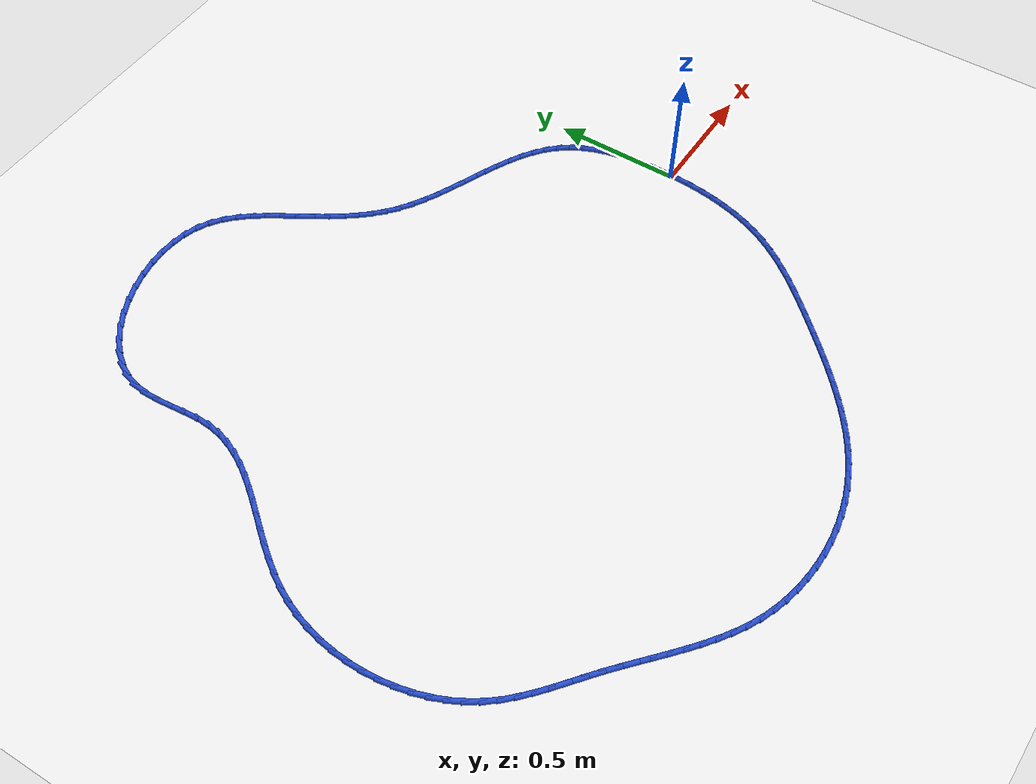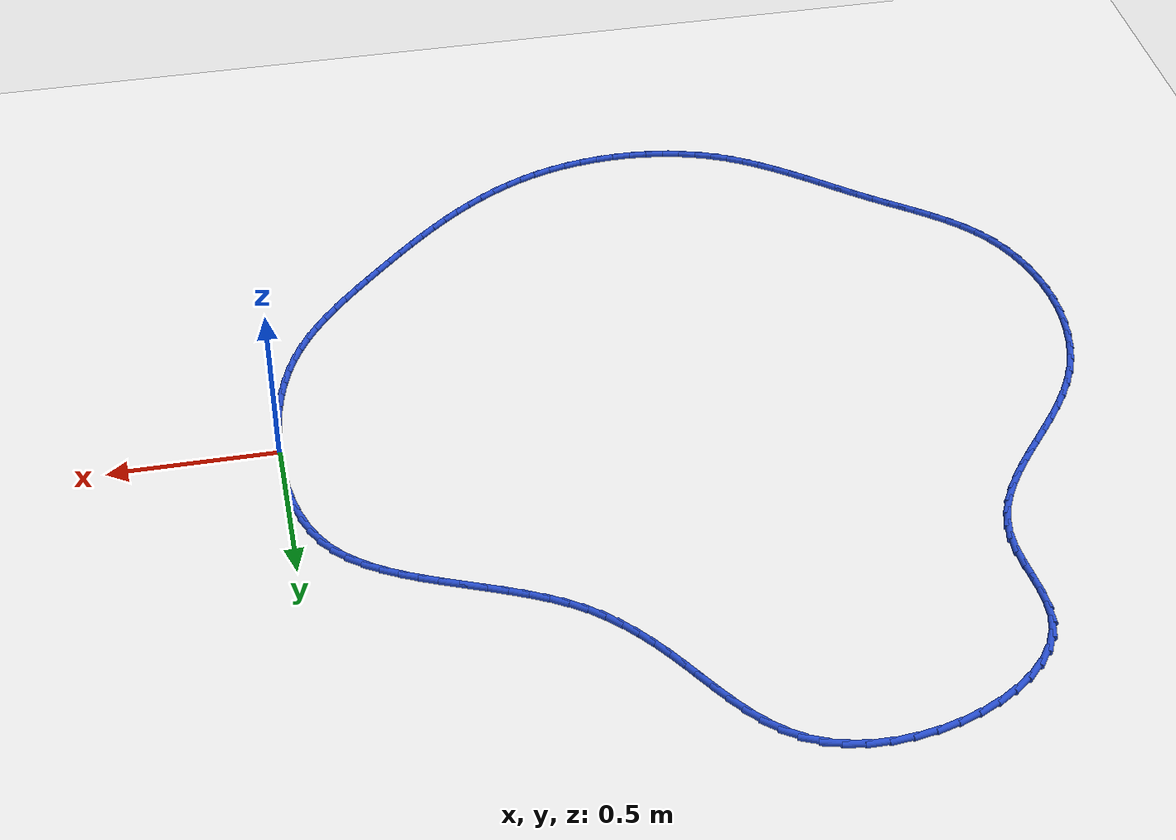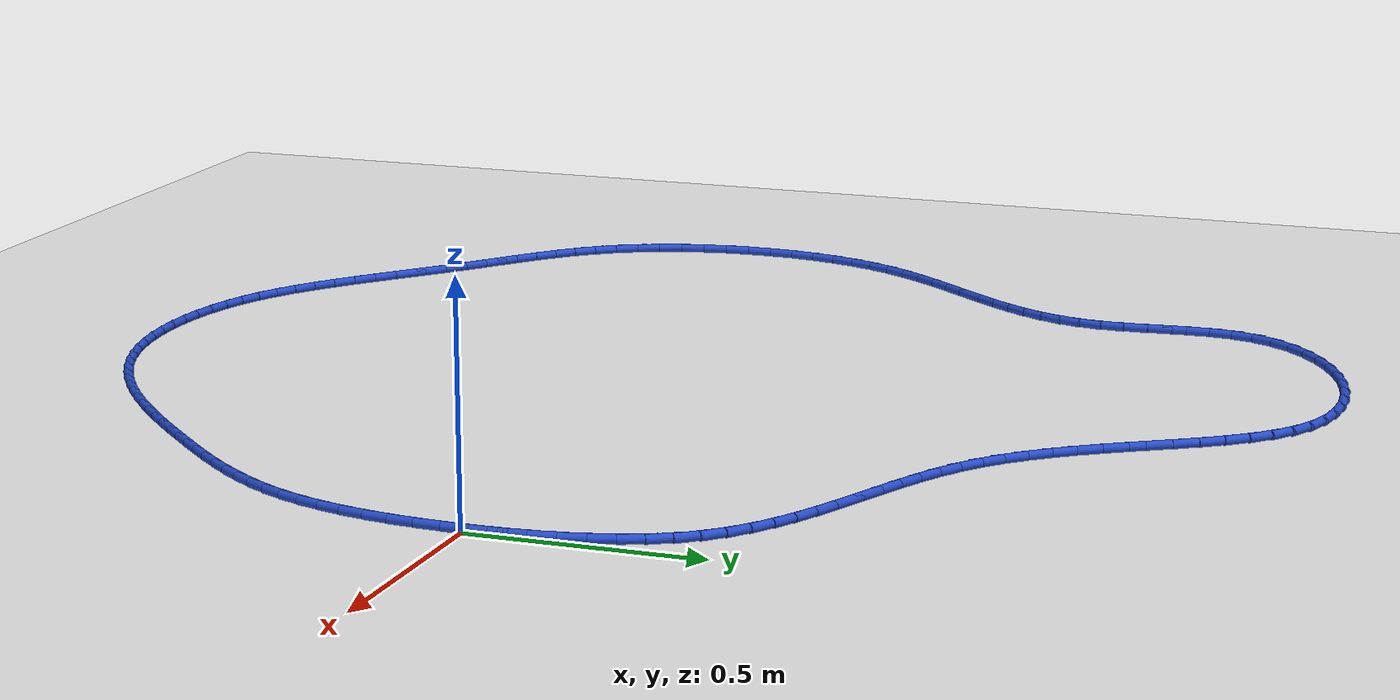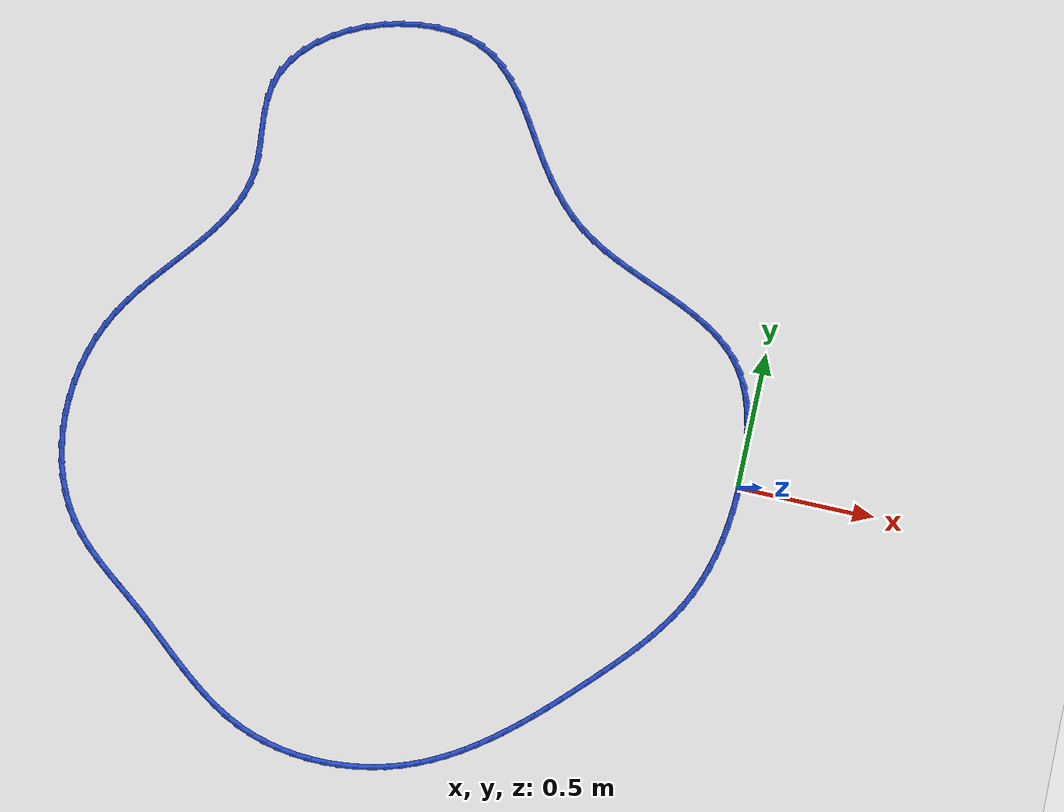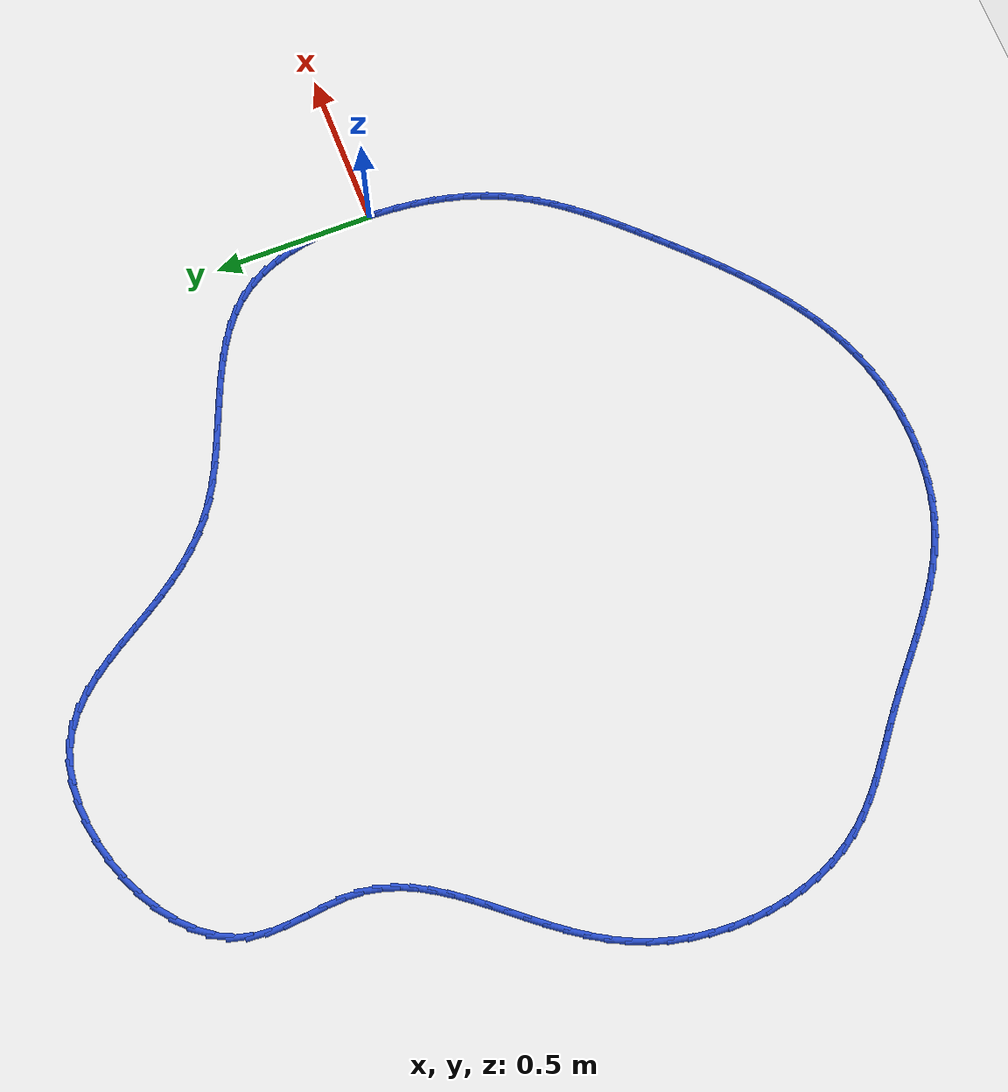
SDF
<sdf version="1.6">
 <world name="default">
  <light name="sun" type="directional">
   <pose>0 0 10 0 -0 0</pose>
   <diffuse>0.8 0.8 0.8 1</diffuse>
   <specular>0.2 0.2 0.2 1</specular>
   <attenuation>
    <range>1000</range>
    <constant>0.9</constant>
    <linear>0.01</linear>
    <quadratic>0.001</quadratic>
   </attenuation>
   <direction>-0.5 0.1 -0.9</direction>
  </light>
  <model name="ground_plane">
   <static>1</static>
   <link name="link">
    <collision name="collision">
     <geometry><plane><normal>0 0 1</normal><size>100 100</size></plane></geometry>
     <surface><friction><ode><mu>100</mu><mu2>50</mu2></ode></friction></surface>
    </collision>
    <visual name="visual">
     <cast_shadows>0</cast_shadows>
     <geometry><plane><normal>0 0 1</normal><size>100 100</size></plane></geometry>
     <material>
      <script><uri>file://media/materials/scripts/gazebo.material</uri><name>Gazebo/WhiteGlow</name></script>
     </material>
    </visual>
   </link>
  </model>
  <gravity>0 0 -9.8</gravity>
  <magnetic_field>6e-06 2.3e-05 -4.2e-05</magnetic_field>
  <atmosphere type="adiabatic"/>
  <physics name="default_physics" default="0" type="ode">
   <max_step_size>0.001</max_step_size>
   <real_time_factor>1</real_time_factor>
   <real_time_update_rate>1000</real_time_update_rate>
  </physics>
  <scene><ambient>0.4 0.4 0.4 1</ambient><background>0.7 0.7 0.7 1</background><shadows>1</shadows></scene>
  <spherical_coordinates>
   <surface_model>EARTH_WGS84</surface_model>
   <latitude_deg>0</latitude_deg>
   <longitude_deg>0</longitude_deg>
   <elevation>0</elevation>
   <heading_deg>0</heading_deg>
  </spherical_coordinates>
  <model name="line">
   <link name="link_0">
    <pose>-1.6479873021779667e-17 8.326672684688674e-17 0.01 0 1.57 1.5662021222615392</pose>
    <collision name="collision">
     <geometry><cylinder><radius>0.01</radius><length>0.08</length></cylinder></geometry>
    </collision>
    <visual name="visual">
     <material>
      <script><name>Gazebo/Blue</name><uri>file://media/materials/scripts/gazebo.material</uri></script>
     </material>
     <geometry><cylinder><radius>0.01</radius><length>0.08</length></cylinder></geometry>
    </visual>
   </link>
   <link name="link_1">
    <pose>0.00027007987229068966 0.05878666701944535 0.01 0 1.57 -1.5292984742662499</pose>
    <collision name="collision">
     <geometry><cylinder><radius>0.01</radius><length>0.08</length></cylinder></geometry>
    </collision>
    <visual name="visual">
     <material>
      <script><name>Gazebo/Blue</name><uri>file://media/materials/scripts/gazebo.material</uri></script>
     </material>
     <geometry><cylinder><radius>0.01</radius><length>0.08</length></cylinder></geometry>
    </visual>
   </link>
   <link name="link_2">
    <pose>-0.0021745974491319316 0.11766378253622534 0.01 0 1.57 -1.4751828375301648</pose>
    <collision name="collision">
     <geometry><cylinder><radius>0.01</radius><length>0.08</length></cylinder></geometry>
    </collision>
    <visual name="visual">
     <material>
      <script><name>Gazebo/Blue</name><uri>file://media/materials/scripts/gazebo.material</uri></script>
     </material>
     <geometry><cylinder><radius>0.01</radius><length>0.08</length></cylinder></geometry>
    </visual>
   </link>
   <link name="link_3">
    <pose>-0.007760177201594749 0.17590397858146603 0.01 0 1.57 -1.4112414805504845</pose>
    <collision name="collision">
     <geometry><cylinder><radius>0.01</radius><length>0.08</length></cylinder></geometry>
    </collision>
    <visual name="visual">
     <material>
      <script><name>Gazebo/Blue</name><uri>file://media/materials/scripts/gazebo.material</uri></script>
     </material>
     <geometry><cylinder><radius>0.01</radius><length>0.08</length></cylinder></geometry>
    </visual>
   </link>
   <link name="link_4">
    <pose>-0.016912804622424615 0.2327798871862933 0.01 0 1.57 -1.3352927763721705</pose>
    <collision name="collision">
     <geometry><cylinder><radius>0.01</radius><length>0.08</length></cylinder></geometry>
    </collision>
    <visual name="visual">
     <material>
      <script><name>Gazebo/Blue</name><uri>file://media/materials/scripts/gazebo.material</uri></script>
     </material>
     <geometry><cylinder><radius>0.01</radius><length>0.08</length></cylinder></geometry>
    </visual>
   </link>
   <link name="link_5">
    <pose>-0.030058624948948405 0.2875641403818332 0.01 0 1.57 -1.2448359389630692</pose>
    <collision name="collision">
     <geometry><cylinder><radius>0.01</radius><length>0.08</length></cylinder></geometry>
    </collision>
    <visual name="visual">
     <material>
      <script><name>Gazebo/Blue</name><uri>file://media/materials/scripts/gazebo.material</uri></script>
     </material>
     <geometry><cylinder><radius>0.01</radius><length>0.08</length></cylinder></geometry>
    </visual>
   </link>
   <link name="link_6">
    <pose>-0.04762378341849294 0.33952937019921153 0.01 0 1.57 -1.1373081696943355</pose>
    <collision name="collision">
     <geometry><cylinder><radius>0.01</radius><length>0.08</length></cylinder></geometry>
    </collision>
    <visual name="visual">
     <material>
      <script><name>Gazebo/Blue</name><uri>file://media/materials/scripts/gazebo.material</uri></script>
     </material>
     <geometry><cylinder><radius>0.01</radius><length>0.08</length></cylinder></geometry>
    </visual>
   </link>
   <link name="link_7">
    <pose>-0.0700344252683851 0.38794820866955404 0.01 0 1.57 -1.0107063499671178</pose>
    <collision name="collision">
     <geometry><cylinder><radius>0.01</radius><length>0.08</length></cylinder></geometry>
    </collision>
    <visual name="visual">
     <material>
      <script><name>Gazebo/Blue</name><uri>file://media/materials/scripts/gazebo.material</uri></script>
     </material>
     <geometry><cylinder><radius>0.01</radius><length>0.08</length></cylinder></geometry>
    </visual>
   </link>
   <link name="link_8">
    <pose>-0.09771669573595176 0.43209328782398704 0.01 0 1.57 -0.8696762934072503</pose>
    <collision name="collision">
     <geometry><cylinder><radius>0.01</radius><length>0.08</length></cylinder></geometry>
    </collision>
    <visual name="visual">
     <material>
      <script><name>Gazebo/Blue</name><uri>file://media/materials/scripts/gazebo.material</uri></script>
     </material>
     <geometry><cylinder><radius>0.01</radius><length>0.08</length></cylinder></geometry>
    </visual>
   </link>
   <link name="link_9">
    <pose>-0.13093241512899828 0.47143885682973213 0.01 0 1.57 -0.740003260000477</pose>
    <collision name="collision">
     <geometry><cylinder><radius>0.01</radius><length>0.08</length></cylinder></geometry>
    </collision>
    <visual name="visual">
     <material>
      <script><name>Gazebo/Blue</name><uri>file://media/materials/scripts/gazebo.material</uri></script>
     </material>
     <geometry><cylinder><radius>0.01</radius><length>0.08</length></cylinder></geometry>
    </visual>
   </link>
   <link name="link_10">
    <pose>-0.16919554271547965 0.5063767468757516 0.01 0 1.57 -0.6317446489766027</pose>
    <collision name="collision">
     <geometry><cylinder><radius>0.01</radius><length>0.08</length></cylinder></geometry>
    </collision>
    <visual name="visual">
     <material>
      <script><name>Gazebo/Blue</name><uri>file://media/materials/scripts/gazebo.material</uri></script>
     </material>
     <geometry><cylinder><radius>0.01</radius><length>0.08</length></cylinder></geometry>
    </visual>
   </link>
   <link name="link_11">
    <pose>-0.21180739723101927 0.5375596867231008 0.01 0 1.57 -0.5455470708644228</pose>
    <collision name="collision">
     <geometry><cylinder><radius>0.01</radius><length>0.08</length></cylinder></geometry>
    </collision>
    <visual name="visual">
     <material>
      <script><name>Gazebo/Blue</name><uri>file://media/materials/scripts/gazebo.material</uri></script>
     </material>
     <geometry><cylinder><radius>0.01</radius><length>0.08</length></cylinder></geometry>
    </visual>
   </link>
   <link name="link_12">
    <pose>-0.25806928252685596 0.5656404233951103 0.01 0 1.57 -0.4801653615835078</pose>
    <collision name="collision">
     <geometry><cylinder><radius>0.01</radius><length>0.08</length></cylinder></geometry>
    </collision>
    <visual name="visual">
     <material>
      <script><name>Gazebo/Blue</name><uri>file://media/materials/scripts/gazebo.material</uri></script>
     </material>
     <geometry><cylinder><radius>0.01</radius><length>0.08</length></cylinder></geometry>
    </visual>
   </link>
   <link name="link_13">
    <pose>-0.3072825024542286 0.5912717039151104 0.01 0 1.57 -0.43370604463463086</pose>
    <collision name="collision">
     <geometry><cylinder><radius>0.01</radius><length>0.08</length></cylinder></geometry>
    </collision>
    <visual name="visual">
     <material>
      <script><name>Gazebo/Blue</name><uri>file://media/materials/scripts/gazebo.material</uri></script>
     </material>
     <geometry><cylinder><radius>0.01</radius><length>0.08</length></cylinder></geometry>
    </visual>
   </link>
   <link name="link_14">
    <pose>-0.35874836086437584 0.6151062753064315 0.01 0 1.57 -0.4043791909685627</pose>
    <collision name="collision">
     <geometry><cylinder><radius>0.01</radius><length>0.08</length></cylinder></geometry>
    </collision>
    <visual name="visual">
     <material>
      <script><name>Gazebo/Blue</name><uri>file://media/materials/scripts/gazebo.material</uri></script>
     </material>
     <geometry><cylinder><radius>0.01</radius><length>0.08</length></cylinder></geometry>
    </visual>
   </link>
   <link name="link_15">
    <pose>-0.4117681616085368 0.6377968845924039 0.01 0 1.57 -0.3908538279553057</pose>
    <collision name="collision">
     <geometry><cylinder><radius>0.01</radius><length>0.08</length></cylinder></geometry>
    </collision>
    <visual name="visual">
     <material>
      <script><name>Gazebo/Blue</name><uri>file://media/materials/scripts/gazebo.material</uri></script>
     </material>
     <geometry><cylinder><radius>0.01</radius><length>0.08</length></cylinder></geometry>
    </visual>
   </link>
   <link name="link_16">
    <pose>-0.46564320853795 0.6599962787963579 0.01 0 1.57 -0.39238792775715886</pose>
    <collision name="collision">
     <geometry><cylinder><radius>0.01</radius><length>0.08</length></cylinder></geometry>
    </collision>
    <visual name="visual">
     <material>
      <script><name>Gazebo/Blue</name><uri>file://media/materials/scripts/gazebo.material</uri></script>
     </material>
     <geometry><cylinder><radius>0.01</radius><length>0.08</length></cylinder></geometry>
    </visual>
   </link>
   <link name="link_17">
    <pose>-0.5196748055038544 0.6823572049416239 0.01 0 1.57 -0.40885184260643354</pose>
    <collision name="collision">
     <geometry><cylinder><radius>0.01</radius><length>0.08</length></cylinder></geometry>
    </collision>
    <visual name="visual">
     <material>
      <script><name>Gazebo/Blue</name><uri>file://media/materials/scripts/gazebo.material</uri></script>
     </material>
     <geometry><cylinder><radius>0.01</radius><length>0.08</length></cylinder></geometry>
    </visual>
   </link>
   <link name="link_18">
    <pose>-0.573164256357489 0.7055324100515323 0.01 0 1.57 -0.44069857170927607</pose>
    <collision name="collision">
     <geometry><cylinder><radius>0.01</radius><length>0.08</length></cylinder></geometry>
    </collision>
    <visual name="visual">
     <material>
      <script><name>Gazebo/Blue</name><uri>file://media/materials/scripts/gazebo.material</uri></script>
     </material>
     <geometry><cylinder><radius>0.01</radius><length>0.08</length></cylinder></geometry>
    </visual>
   </link>
   <link name="link_19">
    <pose>-0.6254128649500923 0.7301746411494137 0.01 0 1.57 -0.4888811779173968</pose>
    <collision name="collision">
     <geometry><cylinder><radius>0.01</radius><length>0.08</length></cylinder></geometry>
    </collision>
    <visual name="visual">
     <material>
      <script><name>Gazebo/Blue</name><uri>file://media/materials/scripts/gazebo.material</uri></script>
     </material>
     <geometry><cylinder><radius>0.01</radius><length>0.08</length></cylinder></geometry>
    </visual>
   </link>
   <link name="link_20">
    <pose>-0.6757219351329034 0.7569366452585979 0.01 0 1.57 -0.5546714894485142</pose>
    <collision name="collision">
     <geometry><cylinder><radius>0.01</radius><length>0.08</length></cylinder></geometry>
    </collision>
    <visual name="visual">
     <material>
      <script><name>Gazebo/Blue</name><uri>file://media/materials/scripts/gazebo.material</uri></script>
     </material>
     <geometry><cylinder><radius>0.01</radius><length>0.08</length></cylinder></geometry>
    </visual>
   </link>
   <link name="link_21">
    <pose>-0.7233927707571608 0.7864711694024156 0.01 0 1.57 -0.6387427131420124</pose>
    <collision name="collision">
     <geometry><cylinder><radius>0.01</radius><length>0.08</length></cylinder></geometry>
    </collision>
    <visual name="visual">
     <material>
      <script><name>Gazebo/Blue</name><uri>file://media/materials/scripts/gazebo.material</uri></script>
     </material>
     <geometry><cylinder><radius>0.01</radius><length>0.08</length></cylinder></geometry>
    </visual>
   </link>
   <link name="link_22">
    <pose>-0.7677500149901675 0.8194104770849994 0.01 0 1.57 -0.7281159391969414</pose>
    <collision name="collision">
     <geometry><cylinder><radius>0.01</radius><length>0.08</length></cylinder></geometry>
    </collision>
    <visual name="visual">
     <material>
      <script><name>Gazebo/Blue</name><uri>file://media/materials/scripts/gazebo.material</uri></script>
     </material>
     <geometry><cylinder><radius>0.01</radius><length>0.08</length></cylinder></geometry>
    </visual>
   </link>
   <link name="link_23">
    <pose>-0.8086760847177507 0.8558973072400081 0.01 0 1.57 -0.8076830214042869</pose>
    <collision name="collision">
     <geometry><cylinder><radius>0.01</radius><length>0.08</length></cylinder></geometry>
    </collision>
    <visual name="visual">
     <material>
      <script><name>Gazebo/Blue</name><uri>file://media/materials/scripts/gazebo.material</uri></script>
     </material>
     <geometry><cylinder><radius>0.01</radius><length>0.08</length></cylinder></geometry>
    </visual>
   </link>
   <link name="link_24">
    <pose>-0.8466230751127204 0.8955744263042222 0.01 0 1.57 -0.8755111262053662</pose>
    <collision name="collision">
     <geometry><cylinder><radius>0.01</radius><length>0.08</length></cylinder></geometry>
    </collision>
    <visual name="visual">
     <material>
      <script><name>Gazebo/Blue</name><uri>file://media/materials/scripts/gazebo.material</uri></script>
     </material>
     <geometry><cylinder><radius>0.01</radius><length>0.08</length></cylinder></geometry>
    </visual>
   </link>
   <link name="link_25">
    <pose>-0.8820688019105202 0.938062027317797 0.01 0 1.57 -0.9311021314186065</pose>
    <collision name="collision">
     <geometry><cylinder><radius>0.01</radius><length>0.08</length></cylinder></geometry>
    </collision>
    <visual name="visual">
     <material>
      <script><name>Gazebo/Blue</name><uri>file://media/materials/scripts/gazebo.material</uri></script>
     </material>
     <geometry><cylinder><radius>0.01</radius><length>0.08</length></cylinder></geometry>
    </visual>
   </link>
   <link name="link_26">
    <pose>-0.9154910808465938 0.9829803033208877 0.01 0 1.57 -0.9745282691185173</pose>
    <collision name="collision">
     <geometry><cylinder><radius>0.01</radius><length>0.08</length></cylinder></geometry>
    </collision>
    <visual name="visual">
     <material>
      <script><name>Gazebo/Blue</name><uri>file://media/materials/scripts/gazebo.material</uri></script>
     </material>
     <geometry><cylinder><radius>0.01</radius><length>0.08</length></cylinder></geometry>
    </visual>
   </link>
   <link name="link_27">
    <pose>-0.9473677276563846 1.0299494473536488 0.01 0 1.57 -1.0057101286934689</pose>
    <collision name="collision">
     <geometry><cylinder><radius>0.01</radius><length>0.08</length></cylinder></geometry>
    </collision>
    <visual name="visual">
     <material>
      <script><name>Gazebo/Blue</name><uri>file://media/materials/scripts/gazebo.material</uri></script>
     </material>
     <geometry><cylinder><radius>0.01</radius><length>0.08</length></cylinder></geometry>
    </visual>
   </link>
   <link name="link_28">
    <pose>-0.9781893022507785 1.078559496578281 0.01 0 1.57 -1.0185991414400046</pose>
    <collision name="collision">
     <geometry><cylinder><radius>0.01</radius><length>0.08</length></cylinder></geometry>
    </collision>
    <visual name="visual">
     <material>
      <script><name>Gazebo/Blue</name><uri>file://media/materials/scripts/gazebo.material</uri></script>
     </material>
     <geometry><cylinder><radius>0.01</radius><length>0.08</length></cylinder></geometry>
    </visual>
   </link>
   <link name="link_29">
    <pose>-1.0086300918626143 1.1279657437733064 0.01 0 1.57 -1.0088647498278904</pose>
    <collision name="collision">
     <geometry><cylinder><radius>0.01</radius><length>0.08</length></cylinder></geometry>
    </collision>
    <visual name="visual">
     <material>
      <script><name>Gazebo/Blue</name><uri>file://media/materials/scripts/gazebo.material</uri></script>
     </material>
     <geometry><cylinder><radius>0.01</radius><length>0.08</length></cylinder></geometry>
    </visual>
   </link>
   <link name="link_30">
    <pose>-1.0395023385221558 1.1769970464721076 0.01 0 1.57 -0.9760036157077159</pose>
    <collision name="collision">
     <geometry><cylinder><radius>0.01</radius><length>0.08</length></cylinder></geometry>
    </collision>
    <visual name="visual">
     <material>
      <script><name>Gazebo/Blue</name><uri>file://media/materials/scripts/gazebo.material</uri></script>
     </material>
     <geometry><cylinder><radius>0.01</radius><length>0.08</length></cylinder></geometry>
    </visual>
   </link>
   <link name="link_31">
    <pose>-1.0716216376843974 1.224474327173948 0.01 0 1.57 -0.9184320580696458</pose>
    <collision name="collision">
     <geometry><cylinder><radius>0.01</radius><length>0.08</length></cylinder></geometry>
    </collision>
    <visual name="visual">
     <material>
      <script><name>Gazebo/Blue</name><uri>file://media/materials/scripts/gazebo.material</uri></script>
     </material>
     <geometry><cylinder><radius>0.01</radius><length>0.08</length></cylinder></geometry>
    </visual>
   </link>
   <link name="link_32">
    <pose>-1.1058035848043337 1.269218508378093 0.01 0 1.57 -0.8337838807462441</pose>
    <collision name="collision">
     <geometry><cylinder><radius>0.01</radius><length>0.08</length></cylinder></geometry>
    </collision>
    <visual name="visual">
     <material>
      <script><name>Gazebo/Blue</name><uri>file://media/materials/scripts/gazebo.material</uri></script>
     </material>
     <geometry><cylinder><radius>0.01</radius><length>0.08</length></cylinder></geometry>
    </visual>
   </link>
   <link name="link_33">
    <pose>-1.1428637753369593 1.310050512583806 0.01 0 1.57 -0.7199542133017709</pose>
    <collision name="collision">
     <geometry><cylinder><radius>0.01</radius><length>0.08</length></cylinder></geometry>
    </collision>
    <visual name="visual">
     <material>
      <script><name>Gazebo/Blue</name><uri>file://media/materials/scripts/gazebo.material</uri></script>
     </material>
     <geometry><cylinder><radius>0.01</radius><length>0.08</length></cylinder></geometry>
    </visual>
   </link>
   <link name="link_34">
    <pose>-1.1836178047372685 1.3457912622903516 0.01 0 1.57 -0.5771384441373236</pose>
    <collision name="collision">
     <geometry><cylinder><radius>0.01</radius><length>0.08</length></cylinder></geometry>
    </collision>
    <visual name="visual">
     <material>
      <script><name>Gazebo/Blue</name><uri>file://media/materials/scripts/gazebo.material</uri></script>
     </material>
     <geometry><cylinder><radius>0.01</radius><length>0.08</length></cylinder></geometry>
    </visual>
   </link>
   <link name="link_35">
    <pose>-1.228881268460256 1.3752616799969937 0.01 0 1.57 -0.41180955839088135</pose>
    <collision name="collision">
     <geometry><cylinder><radius>0.01</radius><length>0.08</length></cylinder></geometry>
    </collision>
    <visual name="visual">
     <material>
      <script><name>Gazebo/Blue</name><uri>file://media/materials/scripts/gazebo.material</uri></script>
     </material>
     <geometry><cylinder><radius>0.01</radius><length>0.08</length></cylinder></geometry>
    </visual>
   </link>
   <link name="link_36">
    <pose>-1.2794076821355773 1.3973308238242974 0.01 0 1.57 -0.2529647030927741</pose>
    <collision name="collision">
     <geometry><cylinder><radius>0.01</radius><length>0.08</length></cylinder></geometry>
    </collision>
    <visual name="visual">
     <material>
      <script><name>Gazebo/Blue</name><uri>file://media/materials/scripts/gazebo.material</uri></script>
     </material>
     <geometry><cylinder><radius>0.01</radius><length>0.08</length></cylinder></geometry>
    </visual>
   </link>
   <link name="link_37">
    <pose>-1.3349064050537924 1.4116773726326322 0.01 0 1.57 -0.11705845314525713</pose>
    <collision name="collision">
     <geometry><cylinder><radius>0.01</radius><length>0.08</length></cylinder></geometry>
    </collision>
    <visual name="visual">
     <material>
      <script><name>Gazebo/Blue</name><uri>file://media/materials/scripts/gazebo.material</uri></script>
     </material>
     <geometry><cylinder><radius>0.01</radius><length>0.08</length></cylinder></geometry>
    </visual>
   </link>
   <link name="link_38">
    <pose>-1.394219648241005 1.418652377026995 0.01 0 1.57 0.0004052203901564745</pose>
    <collision name="collision">
     <geometry><cylinder><radius>0.01</radius><length>0.08</length></cylinder></geometry>
    </collision>
    <visual name="visual">
     <material>
      <script><name>Gazebo/Blue</name><uri>file://media/materials/scripts/gazebo.material</uri></script>
     </material>
     <geometry><cylinder><radius>0.01</radius><length>0.08</length></cylinder></geometry>
    </visual>
   </link>
   <link name="link_39">
    <pose>-1.4561633278733694 1.4186272761835927 0.01 0 1.57 0.1045825411278735</pose>
    <collision name="collision">
     <geometry><cylinder><radius>0.01</radius><length>0.08</length></cylinder></geometry>
    </collision>
    <visual name="visual">
     <material>
      <script><name>Gazebo/Blue</name><uri>file://media/materials/scripts/gazebo.material</uri></script>
     </material>
     <geometry><cylinder><radius>0.01</radius><length>0.08</length></cylinder></geometry>
    </visual>
   </link>
   <link name="link_40">
    <pose>-1.5195533601270377 1.4119735092786316 0.01 0 1.57 0.20012122598356696</pose>
    <collision name="collision">
     <geometry><cylinder><radius>0.01</radius><length>0.08</length></cylinder></geometry>
    </collision>
    <visual name="visual">
     <material>
      <script><name>Gazebo/Blue</name><uri>file://media/materials/scripts/gazebo.material</uri></script>
     </material>
     <geometry><cylinder><radius>0.01</radius><length>0.08</length></cylinder></geometry>
    </visual>
   </link>
   <link name="link_41">
    <pose>-1.5832056611781642 1.3990625154883178 0.01 0 1.57 0.2911296851606142</pose>
    <collision name="collision">
     <geometry><cylinder><radius>0.01</radius><length>0.08</length></cylinder></geometry>
    </collision>
    <visual name="visual">
     <material>
      <script><name>Gazebo/Blue</name><uri>file://media/materials/scripts/gazebo.material</uri></script>
     </material>
     <geometry><cylinder><radius>0.01</radius><length>0.08</length></cylinder></geometry>
    </visual>
   </link>
   <link name="link_42">
    <pose>-1.6459361472029004 1.380265733988858 0.01 0 1.57 0.38137767752808127</pose>
    <collision name="collision">
     <geometry><cylinder><radius>0.01</radius><length>0.08</length></cylinder></geometry>
    </collision>
    <visual name="visual">
     <material>
      <script><name>Gazebo/Blue</name><uri>file://media/materials/scripts/gazebo.material</uri></script>
     </material>
     <geometry><cylinder><radius>0.01</radius><length>0.08</length></cylinder></geometry>
    </visual>
   </link>
   <link name="link_43">
    <pose>-1.7065607343773994 1.355954603956458 0.01 0 1.57 0.4745647357248217</pose>
    <collision name="collision">
     <geometry><cylinder><radius>0.01</radius><length>0.08</length></cylinder></geometry>
    </collision>
    <visual name="visual">
     <material>
      <script><name>Gazebo/Blue</name><uri>file://media/materials/scripts/gazebo.material</uri></script>
     </material>
     <geometry><cylinder><radius>0.01</radius><length>0.08</length></cylinder></geometry>
    </visual>
   </link>
   <link name="link_44">
    <pose>-1.7638953388778156 1.3265005645673238 0.01 0 1.57 0.5745932325230839</pose>
    <collision name="collision">
     <geometry><cylinder><radius>0.01</radius><length>0.08</length></cylinder></geometry>
    </collision>
    <visual name="visual">
     <material>
      <script><name>Gazebo/Blue</name><uri>file://media/materials/scripts/gazebo.material</uri></script>
     </material>
     <geometry><cylinder><radius>0.01</radius><length>0.08</length></cylinder></geometry>
    </visual>
   </link>
   <link name="link_45">
    <pose>-1.8167558768803003 1.292275054997662 0.01 0 1.57 0.6857981003588236</pose>
    <collision name="collision">
     <geometry><cylinder><radius>0.01</radius><length>0.08</length></cylinder></geometry>
    </collision>
    <visual name="visual">
     <material>
      <script><name>Gazebo/Blue</name><uri>file://media/materials/scripts/gazebo.material</uri></script>
     </material>
     <geometry><cylinder><radius>0.01</radius><length>0.08</length></cylinder></geometry>
    </visual>
   </link>
   <link name="link_46">
    <pose>-1.8639582645610073 1.2536495144236786 0.01 0 1.57 0.8130246761680432</pose>
    <collision name="collision">
     <geometry><cylinder><radius>0.01</radius><length>0.08</length></cylinder></geometry>
    </collision>
    <visual name="visual">
     <material>
      <script><name>Gazebo/Blue</name><uri>file://media/materials/scripts/gazebo.material</uri></script>
     </material>
     <geometry><cylinder><radius>0.01</radius><length>0.08</length></cylinder></geometry>
    </visual>
   </link>
   <link name="link_47">
    <pose>-1.904318418096089 1.21099538202158 0.01 0 1.57 0.9612896526685911</pose>
    <collision name="collision">
     <geometry><cylinder><radius>0.01</radius><length>0.08</length></cylinder></geometry>
    </collision>
    <visual name="visual">
     <material>
      <script><name>Gazebo/Blue</name><uri>file://media/materials/scripts/gazebo.material</uri></script>
     </material>
     <geometry><cylinder><radius>0.01</radius><length>0.08</length></cylinder></geometry>
    </visual>
   </link>
   <link name="link_48">
    <pose>-1.9366522536617 1.1646840969675722 0.01 0 1.57 1.1345306995879232</pose>
    <collision name="collision">
     <geometry><cylinder><radius>0.01</radius><length>0.08</length></cylinder></geometry>
    </collision>
    <visual name="visual">
     <material>
      <script><name>Gazebo/Blue</name><uri>file://media/materials/scripts/gazebo.material</uri></script>
     </material>
     <geometry><cylinder><radius>0.01</radius><length>0.08</length></cylinder></geometry>
    </visual>
   </link>
   <link name="link_49">
    <pose>-1.9597756874339909 1.1150870984378622 0.01 0 1.57 1.330270247468746</pose>
    <collision name="collision">
     <geometry><cylinder><radius>0.01</radius><length>0.08</length></cylinder></geometry>
    </collision>
    <visual name="visual">
     <material>
      <script><name>Gazebo/Blue</name><uri>file://media/materials/scripts/gazebo.material</uri></script>
     </material>
     <geometry><cylinder><radius>0.01</radius><length>0.08</length></cylinder></geometry>
    </visual>
   </link>
   <link name="link_50">
    <pose>-1.9726511391690944 1.0625930187568984 0.01 0 1.57 1.500414735692357</pose>
    <collision name="collision">
     <geometry><cylinder><radius>0.01</radius><length>0.08</length></cylinder></geometry>
    </collision>
    <visual name="visual">
     <material>
      <script><name>Gazebo/Blue</name><uri>file://media/materials/scripts/gazebo.material</uri></script>
     </material>
     <geometry><cylinder><radius>0.01</radius><length>0.08</length></cylinder></geometry>
    </visual>
   </link>
   <link name="link_51">
    <pose>-1.976509937758696 1.0078567614974099 0.01 0 1.57 -1.5326817299557682</pose>
    <collision name="collision">
     <geometry><cylinder><radius>0.01</radius><length>0.08</length></cylinder></geometry>
    </collision>
    <visual name="visual">
     <material>
      <script><name>Gazebo/Blue</name><uri>file://media/materials/scripts/gazebo.material</uri></script>
     </material>
     <geometry><cylinder><radius>0.01</radius><length>0.08</length></cylinder></geometry>
    </visual>
   </link>
   <link name="link_52">
    <pose>-1.97437014484478 0.9517429149446172 0.01 0 1.57 -1.481457273964573</pose>
    <collision name="collision">
     <geometry><cylinder><radius>0.01</radius><length>0.08</length></cylinder></geometry>
    </collision>
    <visual name="visual">
     <material>
      <script><name>Gazebo/Blue</name><uri>file://media/materials/scripts/gazebo.material</uri></script>
     </material>
     <geometry><cylinder><radius>0.01</radius><length>0.08</length></cylinder></geometry>
    </visual>
   </link>
   <link name="link_53">
    <pose>-1.9692981615954812 0.8951217403416268 0.01 0 1.57 -1.483250908545958</pose>
    <collision name="collision">
     <geometry><cylinder><radius>0.01</radius><length>0.08</length></cylinder></geometry>
    </collision>
    <visual name="visual">
     <material>
      <script><name>Gazebo/Blue</name><uri>file://media/materials/scripts/gazebo.material</uri></script>
     </material>
     <geometry><cylinder><radius>0.01</radius><length>0.08</length></cylinder></geometry>
    </visual>
   </link>
   <link name="link_54">
    <pose>-1.9643603891789354 0.8388634989315444 0.01 0 1.57 -1.5392364514164134</pose>
    <collision name="collision">
     <geometry><cylinder><radius>0.01</radius><length>0.08</length></cylinder></geometry>
    </collision>
    <visual name="visual">
     <material>
      <script><name>Gazebo/Blue</name><uri>file://media/materials/scripts/gazebo.material</uri></script>
     </material>
     <geometry><cylinder><radius>0.01</radius><length>0.08</length></cylinder></geometry>
    </visual>
   </link>
   <link name="link_55">
    <pose>-1.9626232287632783 0.7838384519574751 0.01 0 1.57 1.487653254144628</pose>
    <collision name="collision">
     <geometry><cylinder><radius>0.01</radius><length>0.08</length></cylinder></geometry>
    </collision>
    <visual name="visual">
     <material>
      <script><name>Gazebo/Blue</name><uri>file://media/materials/scripts/gazebo.material</uri></script>
     </material>
     <geometry><cylinder><radius>0.01</radius><length>0.08</length></cylinder></geometry>
    </visual>
   </link>
   <link name="link_56">
    <pose>-1.9670364825727251 0.7308805841617209 0.01 0 1.57 1.3481107005879835</pose>
    <collision name="collision">
     <geometry><cylinder><radius>0.01</radius><length>0.08</length></cylinder></geometry>
    </collision>
    <visual name="visual">
     <material>
      <script><name>Gazebo/Blue</name><uri>file://media/materials/scripts/gazebo.material</uri></script>
     </material>
     <geometry><cylinder><radius>0.01</radius><length>0.08</length></cylinder></geometry>
    </visual>
   </link>
   <link name="link_57">
    <pose>-1.9785147561654568 0.6801906857565853 0.01 0 1.57 1.222075824554182</pose>
    <collision name="collision">
     <geometry><cylinder><radius>0.01</radius><length>0.08</length></cylinder></geometry>
    </collision>
    <visual name="visual">
     <material>
      <script><name>Gazebo/Blue</name><uri>file://media/materials/scripts/gazebo.material</uri></script>
     </material>
     <geometry><cylinder><radius>0.01</radius><length>0.08</length></cylinder></geometry>
    </visual>
   </link>
   <link name="link_58">
    <pose>-1.9962426521378058 0.631431304910939 0.01 0 1.57 1.11539981759588</pose>
    <collision name="collision">
     <geometry><cylinder><radius>0.01</radius><length>0.08</length></cylinder></geometry>
    </collision>
    <visual name="visual">
     <material>
      <script><name>Gazebo/Blue</name><uri>file://media/materials/scripts/gazebo.material</uri></script>
     </material>
     <geometry><cylinder><radius>0.01</radius><length>0.08</length></cylinder></geometry>
    </visual>
   </link>
   <link name="link_59">
    <pose>-2.0193497184015405 0.5842478610681083 0.01 0 1.57 1.0297606252783384</pose>
    <collision name="collision">
     <geometry><cylinder><radius>0.01</radius><length>0.08</length></cylinder></geometry>
    </collision>
    <visual name="visual">
     <material>
      <script><name>Gazebo/Blue</name><uri>file://media/materials/scripts/gazebo.material</uri></script>
     </material>
     <geometry><cylinder><radius>0.01</radius><length>0.08</length></cylinder></geometry>
    </visual>
   </link>
   <link name="link_60">
    <pose>-2.0469655028684293 0.5382857736714214 0.01 0 1.57 0.9647388783125529</pose>
    <collision name="collision">
     <geometry><cylinder><radius>0.01</radius><length>0.08</length></cylinder></geometry>
    </collision>
    <visual name="visual">
     <material>
      <script><name>Gazebo/Blue</name><uri>file://media/materials/scripts/gazebo.material</uri></script>
     </material>
     <geometry><cylinder><radius>0.01</radius><length>0.08</length></cylinder></geometry>
    </visual>
   </link>
   <link name="link_61">
    <pose>-2.078219553450241 0.49319046216420487 0.01 0 1.57 0.918956873097289</pose>
    <collision name="collision">
     <geometry><cylinder><radius>0.01</radius><length>0.08</length></cylinder></geometry>
    </collision>
    <visual name="visual">
     <material>
      <script><name>Gazebo/Blue</name><uri>file://media/materials/scripts/gazebo.material</uri></script>
     </material>
     <geometry><cylinder><radius>0.01</radius><length>0.08</length></cylinder></geometry>
    </visual>
   </link>
   <link name="link_62">
    <pose>-2.1122414180587428 0.4486073459897865 0.01 0 1.57 0.8908774530167706</pose>
    <collision name="collision">
     <geometry><cylinder><radius>0.01</radius><length>0.08</length></cylinder></geometry>
    </collision>
    <visual name="visual">
     <material>
      <script><name>Gazebo/Blue</name><uri>file://media/materials/scripts/gazebo.material</uri></script>
     </material>
     <geometry><cylinder><radius>0.01</radius><length>0.08</length></cylinder></geometry>
    </visual>
   </link>
   <link name="link_63">
    <pose>-2.1481606446057038 0.4041818445914933 0.01 0 1.57 0.8792306963401972</pose>
    <collision name="collision">
     <geometry><cylinder><radius>0.01</radius><length>0.08</length></cylinder></geometry>
    </collision>
    <visual name="visual">
     <material>
      <script><name>Gazebo/Blue</name><uri>file://media/materials/scripts/gazebo.material</uri></script>
     </material>
     <geometry><cylinder><radius>0.01</radius><length>0.08</length></cylinder></geometry>
    </visual>
   </link>
   <link name="link_64">
    <pose>-2.185106781002893 0.3595593774126532 0.01 0 1.57 0.8831862889840897</pose>
    <collision name="collision">
     <geometry><cylinder><radius>0.01</radius><length>0.08</length></cylinder></geometry>
    </collision>
    <visual name="visual">
     <material>
      <script><name>Gazebo/Blue</name><uri>file://media/materials/scripts/gazebo.material</uri></script>
     </material>
     <geometry><cylinder><radius>0.01</radius><length>0.08</length></cylinder></geometry>
    </visual>
   </link>
   <link name="link_65">
    <pose>-2.222209375162077 0.314385363896593 0.01 0 1.57 0.9023793598844363</pose>
    <collision name="collision">
     <geometry><cylinder><radius>0.01</radius><length>0.08</length></cylinder></geometry>
    </collision>
    <visual name="visual">
     <material>
      <script><name>Gazebo/Blue</name><uri>file://media/materials/scripts/gazebo.material</uri></script>
     </material>
     <geometry><cylinder><radius>0.01</radius><length>0.08</length></cylinder></geometry>
    </visual>
   </link>
   <link name="link_66">
    <pose>-2.258597974995025 0.26830522348663977 0.01 0 1.57 0.9368461888215276</pose>
    <collision name="collision">
     <geometry><cylinder><radius>0.01</radius><length>0.08</length></cylinder></geometry>
    </collision>
    <visual name="visual">
     <material>
      <script><name>Gazebo/Blue</name><uri>file://media/materials/scripts/gazebo.material</uri></script>
     </material>
     <geometry><cylinder><radius>0.01</radius><length>0.08</length></cylinder></geometry>
    </visual>
   </link>
   <link name="link_67">
    <pose>-2.2934021284135064 0.22096437562612165 0.01 0 1.57 0.9868799111405122</pose>
    <collision name="collision">
     <geometry><cylinder><radius>0.01</radius><length>0.08</length></cylinder></geometry>
    </collision>
    <visual name="visual">
     <material>
      <script><name>Gazebo/Blue</name><uri>file://media/materials/scripts/gazebo.material</uri></script>
     </material>
     <geometry><cylinder><radius>0.01</radius><length>0.08</length></cylinder></geometry>
    </visual>
   </link>
   <link name="link_68">
    <pose>-2.3257513833292895 0.17200823975836516 0.01 0 1.57 1.0527858718921739</pose>
    <collision name="collision">
     <geometry><cylinder><radius>0.01</radius><length>0.08</length></cylinder></geometry>
    </collision>
    <visual name="visual">
     <material>
      <script><name>Gazebo/Blue</name><uri>file://media/materials/scripts/gazebo.material</uri></script>
     </material>
     <geometry><cylinder><radius>0.01</radius><length>0.08</length></cylinder></geometry>
    </visual>
   </link>
   <link name="link_69">
    <pose>-2.35477528765414 0.12108223532669841 0.01 0 1.57 1.1334828373053283</pose>
    <collision name="collision">
     <geometry><cylinder><radius>0.01</radius><length>0.08</length></cylinder></geometry>
    </collision>
    <visual name="visual">
     <material>
      <script><name>Gazebo/Blue</name><uri>file://media/materials/scripts/gazebo.material</uri></script>
     </material>
     <geometry><cylinder><radius>0.01</radius><length>0.08</length></cylinder></geometry>
    </visual>
   </link>
   <link name="link_70">
    <pose>-2.3796496394620337 0.06787537657227873 0.01 0 1.57 1.2173153509362624</pose>
    <collision name="collision">
     <geometry><cylinder><radius>0.01</radius><length>0.08</length></cylinder></geometry>
    </collision>
    <visual name="visual">
     <material>
      <script><name>Gazebo/Blue</name><uri>file://media/materials/scripts/gazebo.material</uri></script>
     </material>
     <geometry><cylinder><radius>0.01</radius><length>0.08</length></cylinder></geometry>
    </visual>
   </link>
   <link name="link_71">
    <pose>-2.400060636283434 0.012557773586718588 0.01 0 1.57 1.2977561322640074</pose>
    <collision name="collision">
     <geometry><cylinder><radius>0.01</radius><length>0.08</length></cylinder></geometry>
    </collision>
    <visual name="visual">
     <material>
      <script><name>Gazebo/Blue</name><uri>file://media/materials/scripts/gazebo.material</uri></script>
     </material>
     <geometry><cylinder><radius>0.01</radius><length>0.08</length></cylinder></geometry>
    </visual>
   </link>
   <link name="link_72">
    <pose>-2.416011267885028 -0.044401859320904895 0.01 0 1.57 1.3755139066346584</pose>
    <collision name="collision">
     <geometry><cylinder><radius>0.01</radius><length>0.08</length></cylinder></geometry>
    </collision>
    <visual name="visual">
     <material>
      <script><name>Gazebo/Blue</name><uri>file://media/materials/scripts/gazebo.material</uri></script>
     </material>
     <geometry><cylinder><radius>0.01</radius><length>0.08</length></cylinder></geometry>
    </visual>
   </link>
   <link name="link_73">
    <pose>-2.4275092697786596 -0.1025303345642172 0.01 0 1.57 1.4514643984773368</pose>
    <collision name="collision">
     <geometry><cylinder><radius>0.01</radius><length>0.08</length></cylinder></geometry>
    </collision>
    <visual name="visual">
     <material>
      <script><name>Gazebo/Blue</name><uri>file://media/materials/scripts/gazebo.material</uri></script>
     </material>
     <geometry><cylinder><radius>0.01</radius><length>0.08</length></cylinder></geometry>
    </visual>
   </link>
   <link name="link_74">
    <pose>-2.434562377476169 -0.1613544645568413 0.01 0 1.57 1.5265221492430665</pose>
    <collision name="collision">
     <geometry><cylinder><radius>0.01</radius><length>0.08</length></cylinder></geometry>
    </collision>
    <visual name="visual">
     <material>
      <script><name>Gazebo/Blue</name><uri>file://media/materials/scripts/gazebo.material</uri></script>
     </material>
     <geometry><cylinder><radius>0.01</radius><length>0.08</length></cylinder></geometry>
    </visual>
   </link>
   <link name="link_75">
    <pose>-2.4371783264893994 -0.22040106171240273 0.01 0 1.57 -1.5399625418408989</pose>
    <collision name="collision">
     <geometry><cylinder><radius>0.01</radius><length>0.08</length></cylinder></geometry>
    </collision>
    <visual name="visual">
     <material>
      <script><name>Gazebo/Blue</name><uri>file://media/materials/scripts/gazebo.material</uri></script>
     </material>
     <geometry><cylinder><radius>0.01</radius><length>0.08</length></cylinder></geometry>
    </visual>
   </link>
   <link name="link_76">
    <pose>-2.4353648523301925 -0.27919693844452603 0.01 0 1.57 -1.463836528066739</pose>
    <collision name="collision">
     <geometry><cylinder><radius>0.01</radius><length>0.08</length></cylinder></geometry>
    </collision>
    <visual name="visual">
     <material>
      <script><name>Gazebo/Blue</name><uri>file://media/materials/scripts/gazebo.material</uri></script>
     </material>
     <geometry><cylinder><radius>0.01</radius><length>0.08</length></cylinder></geometry>
    </visual>
   </link>
   <link name="link_77">
    <pose>-2.429129690510391 -0.3372689071668359 0.01 0 1.57 -1.3857018903241891</pose>
    <collision name="collision">
     <geometry><cylinder><radius>0.01</radius><length>0.08</length></cylinder></geometry>
    </collision>
    <visual name="visual">
     <material>
      <script><name>Gazebo/Blue</name><uri>file://media/materials/scripts/gazebo.material</uri></script>
     </material>
     <geometry><cylinder><radius>0.01</radius><length>0.08</length></cylinder></geometry>
    </visual>
   </link>
   <link name="link_78">
    <pose>-2.4184805765418362 -0.3941437802929578 0.01 0 1.57 -1.3045521455791063</pose>
    <collision name="collision">
     <geometry><cylinder><radius>0.01</radius><length>0.08</length></cylinder></geometry>
    </collision>
    <visual name="visual">
     <material>
      <script><name>Gazebo/Blue</name><uri>file://media/materials/scripts/gazebo.material</uri></script>
     </material>
     <geometry><cylinder><radius>0.01</radius><length>0.08</length></cylinder></geometry>
    </visual>
   </link>
   <link name="link_79">
    <pose>-2.403425245936371 -0.4493483702365147 0.01 0 1.57 -1.2193836283646053</pose>
    <collision name="collision">
     <geometry><cylinder><radius>0.01</radius><length>0.08</length></cylinder></geometry>
    </collision>
    <visual name="visual">
     <material>
      <script><name>Gazebo/Blue</name><uri>file://media/materials/scripts/gazebo.material</uri></script>
     </material>
     <geometry><cylinder><radius>0.01</radius><length>0.08</length></cylinder></geometry>
    </visual>
   </link>
   <link name="link_80">
    <pose>-2.383971434205838 -0.502409489411132 0.01 0 1.57 -1.1292349942059703</pose>
    <collision name="collision">
     <geometry><cylinder><radius>0.01</radius><length>0.08</length></cylinder></geometry>
    </collision>
    <visual name="visual">
     <material>
      <script><name>Gazebo/Blue</name><uri>file://media/materials/scripts/gazebo.material</uri></script>
     </material>
     <geometry><cylinder><radius>0.01</radius><length>0.08</length></cylinder></geometry>
    </visual>
   </link>
   <link name="link_81">
    <pose>-2.3601268768620782 -0.5528539502304342 0.01 0 1.57 -1.0332574866734598</pose>
    <collision name="collision">
     <geometry><cylinder><radius>0.01</radius><length>0.08</length></cylinder></geometry>
    </collision>
    <visual name="visual">
     <material>
      <script><name>Gazebo/Blue</name><uri>file://media/materials/scripts/gazebo.material</uri></script>
     </material>
     <geometry><cylinder><radius>0.01</radius><length>0.08</length></cylinder></geometry>
    </visual>
   </link>
   <link name="link_82">
    <pose>-2.3318993094169347 -0.6002085651080471 0.01 0 1.57 -0.9316572968736174</pose>
    <collision name="collision">
     <geometry><cylinder><radius>0.01</radius><length>0.08</length></cylinder></geometry>
    </collision>
    <visual name="visual">
     <material>
      <script><name>Gazebo/Blue</name><uri>file://media/materials/scripts/gazebo.material</uri></script>
     </material>
     <geometry><cylinder><radius>0.01</radius><length>0.08</length></cylinder></geometry>
    </visual>
   </link>
   <link name="link_83">
    <pose>-2.2993225605934096 -0.6440412706973776 0.01 0 1.57 -0.8375394079106218</pose>
    <collision name="collision">
     <geometry><cylinder><radius>0.01</radius><length>0.08</length></cylinder></geometry>
    </collision>
    <visual name="visual">
     <material>
      <script><name>Gazebo/Blue</name><uri>file://media/materials/scripts/gazebo.material</uri></script>
     </material>
     <geometry><cylinder><radius>0.01</radius><length>0.08</length></cylinder></geometry>
    </visual>
   </link>
   <link name="link_84">
    <pose>-2.262831060730879 -0.6845513723564559 0.01 0 1.57 -0.7624849112829971</pose>
    <collision name="collision">
     <geometry><cylinder><radius>0.01</radius><length>0.08</length></cylinder></geometry>
    </collision>
    <visual name="visual">
     <material>
      <script><name>Gazebo/Blue</name><uri>file://media/materials/scripts/gazebo.material</uri></script>
     </material>
     <geometry><cylinder><radius>0.01</radius><length>0.08</length></cylinder></geometry>
    </visual>
   </link>
   <link name="link_85">
    <pose>-2.2231729096365926 -0.7224325346208994 0.01 0 1.57 -0.7072616555997935</pose>
    <collision name="collision">
     <geometry><cylinder><radius>0.01</radius><length>0.08</length></cylinder></geometry>
    </collision>
    <visual name="visual">
     <material>
      <script><name>Gazebo/Blue</name><uri>file://media/materials/scripts/gazebo.material</uri></script>
     </material>
     <geometry><cylinder><radius>0.01</radius><length>0.08</length></cylinder></geometry>
    </visual>
   </link>
   <link name="link_86">
    <pose>-2.181104587089921 -0.7583916292924147 0.01 0 1.57 -0.6714730307087409</pose>
    <collision name="collision">
     <geometry><cylinder><radius>0.01</radius><length>0.08</length></cylinder></geometry>
    </collision>
    <visual name="visual">
     <material>
      <script><name>Gazebo/Blue</name><uri>file://media/materials/scripts/gazebo.material</uri></script>
     </material>
     <geometry><cylinder><radius>0.01</radius><length>0.08</length></cylinder></geometry>
    </visual>
   </link>
   <link name="link_87">
    <pose>-2.1373825728702367 -0.7931355281727083 0.01 0 1.57 -0.6544707996794008</pose>
    <collision name="collision">
     <geometry><cylinder><radius>0.01</radius><length>0.08</length></cylinder></geometry>
    </collision>
    <visual name="visual">
     <material>
      <script><name>Gazebo/Blue</name><uri>file://media/materials/scripts/gazebo.material</uri></script>
     </material>
     <geometry><cylinder><radius>0.01</radius><length>0.08</length></cylinder></geometry>
    </visual>
   </link>
   <link name="link_88">
    <pose>-2.09276334675691 -0.8273711030634855 0.01 0 1.57 -0.6557431450060648</pose>
    <collision name="collision">
     <geometry><cylinder><radius>0.01</radius><length>0.08</length></cylinder></geometry>
    </collision>
    <visual name="visual">
     <material>
      <script><name>Gazebo/Blue</name><uri>file://media/materials/scripts/gazebo.material</uri></script>
     </material>
     <geometry><cylinder><radius>0.01</radius><length>0.08</length></cylinder></geometry>
    </visual>
   </link>
   <link name="link_89">
    <pose>-2.0480033885293136 -0.8618052257664532 0.01 0 1.57 -0.6742733085509361</pose>
    <collision name="collision">
     <geometry><cylinder><radius>0.01</radius><length>0.08</length></cylinder></geometry>
    </collision>
    <visual name="visual">
     <material>
      <script><name>Gazebo/Blue</name><uri>file://media/materials/scripts/gazebo.material</uri></script>
     </material>
     <geometry><cylinder><radius>0.01</radius><length>0.08</length></cylinder></geometry>
    </visual>
   </link>
   <link name="link_90">
    <pose>-2.003829259722579 -0.897110663490079 0.01 0 1.57 -0.6955656067983585</pose>
    <collision name="collision">
     <geometry><cylinder><radius>0.01</radius><length>0.08</length></cylinder></geometry>
    </collision>
    <visual name="visual">
     <material>
      <script><name>Gazebo/Blue</name><uri>file://media/materials/scripts/gazebo.material</uri></script>
     </material>
     <geometry><cylinder><radius>0.01</radius><length>0.08</length></cylinder></geometry>
    </visual>
   </link>
   <link name="link_91">
    <pose>-1.9604250103140832 -0.9333417602540657 0.01 0 1.57 -0.7070415735488543</pose>
    <collision name="collision">
     <geometry><cylinder><radius>0.01</radius><length>0.08</length></cylinder></geometry>
    </collision>
    <visual name="visual">
     <material>
      <script><name>Gazebo/Blue</name><uri>file://media/materials/scripts/gazebo.material</uri></script>
     </material>
     <geometry><cylinder><radius>0.01</radius><length>0.08</length></cylinder></geometry>
    </visual>
   </link>
   <link name="link_92">
    <pose>-1.9175025264815806 -0.9700146281484743 0.01 0 1.57 -0.7082830364420636</pose>
    <collision name="collision">
     <geometry><cylinder><radius>0.01</radius><length>0.08</length></cylinder></geometry>
    </collision>
    <visual name="visual">
     <material>
      <script><name>Gazebo/Blue</name><uri>file://media/materials/scripts/gazebo.material</uri></script>
     </material>
     <geometry><cylinder><radius>0.01</radius><length>0.08</length></cylinder></geometry>
    </visual>
   </link>
   <link name="link_93">
    <pose>-1.8747579308373246 -1.0066274099605879 0.01 0 1.57 -0.6992004326001741</pose>
    <collision name="collision">
     <geometry><cylinder><radius>0.01</radius><length>0.08</length></cylinder></geometry>
    </collision>
    <visual name="visual">
     <material>
      <script><name>Gazebo/Blue</name><uri>file://media/materials/scripts/gazebo.material</uri></script>
     </material>
     <geometry><cylinder><radius>0.01</radius><length>0.08</length></cylinder></geometry>
    </visual>
   </link>
   <link name="link_94">
    <pose>-1.8318873459935687 -1.0426782484776895 0.01 0 1.57 -0.6796038084589646</pose>
    <collision name="collision">
     <geometry><cylinder><radius>0.01</radius><length>0.08</length></cylinder></geometry>
    </collision>
    <visual name="visual">
     <material>
      <script><name>Gazebo/Blue</name><uri>file://media/materials/scripts/gazebo.material</uri></script>
     </material>
     <geometry><cylinder><radius>0.01</radius><length>0.08</length></cylinder></geometry>
    </visual>
   </link>
   <link name="link_95">
    <pose>-1.788586894562568 -1.0776652864870633 0.01 0 1.57 -0.649227998624624</pose>
    <collision name="collision">
     <geometry><cylinder><radius>0.01</radius><length>0.08</length></cylinder></geometry>
    </collision>
    <visual name="visual">
     <material>
      <script><name>Gazebo/Blue</name><uri>file://media/materials/scripts/gazebo.material</uri></script>
     </material>
     <geometry><cylinder><radius>0.01</radius><length>0.08</length></cylinder></geometry>
    </visual>
   </link>
   <link name="link_96">
    <pose>-1.744552699156577 -1.1110866667759907 0.01 0 1.57 -0.6077953881525934</pose>
    <collision name="collision">
     <geometry><cylinder><radius>0.01</radius><length>0.08</length></cylinder></geometry>
    </collision>
    <visual name="visual">
     <material>
      <script><name>Gazebo/Blue</name><uri>file://media/materials/scripts/gazebo.material</uri></script>
     </material>
     <geometry><cylinder><radius>0.01</radius><length>0.08</length></cylinder></geometry>
    </visual>
   </link>
   <link name="link_97">
    <pose>-1.6994808823878493 -1.1424405321317557 0.01 0 1.57 -0.5551239194677678</pose>
    <collision name="collision">
     <geometry><cylinder><radius>0.01</radius><length>0.08</length></cylinder></geometry>
    </collision>
    <visual name="visual">
     <material>
      <script><name>Gazebo/Blue</name><uri>file://media/materials/scripts/gazebo.material</uri></script>
     </material>
     <geometry><cylinder><radius>0.01</radius><length>0.08</length></cylinder></geometry>
    </visual>
   </link>
   <link name="link_98">
    <pose>-1.6530675668686405 -1.1712250253416416 0.01 0 1.57 -0.49128415737784753</pose>
    <collision name="collision">
     <geometry><cylinder><radius>0.01</radius><length>0.08</length></cylinder></geometry>
    </collision>
    <visual name="visual">
     <material>
      <script><name>Gazebo/Blue</name><uri>file://media/materials/scripts/gazebo.material</uri></script>
     </material>
     <geometry><cylinder><radius>0.01</radius><length>0.08</length></cylinder></geometry>
    </visual>
   </link>
   <link name="link_99">
    <pose>-1.605008875211203 -1.1969382891929308 0.01 0 1.57 -0.41680457798762716</pose>
    <collision name="collision">
     <geometry><cylinder><radius>0.01</radius><length>0.08</length></cylinder></geometry>
    </collision>
    <visual name="visual">
     <material>
      <script><name>Gazebo/Blue</name><uri>file://media/materials/scripts/gazebo.material</uri></script>
     </material>
     <geometry><cylinder><radius>0.01</radius><length>0.08</length></cylinder></geometry>
    </visual>
   </link>
   <link name="link_100">
    <pose>-1.5550014121170057 -1.2190788593980357 0.01 0 1.57 -0.3363887432320146</pose>
    <collision name="collision">
     <geometry><cylinder><radius>0.01</radius><length>0.08</length></cylinder></geometry>
    </collision>
    <visual name="visual">
     <material>
      <script><name>Gazebo/Blue</name><uri>file://media/materials/scripts/gazebo.material</uri></script>
     </material>
     <geometry><cylinder><radius>0.01</radius><length>0.08</length></cylinder></geometry>
    </visual>
   </link>
   <link name="link_101">
    <pose>-1.5029200888723342 -1.237290599827893 0.01 0 1.57 -0.2594275384594313</pose>
    <collision name="collision">
     <geometry><cylinder><radius>0.01</radius><length>0.08</length></cylinder></geometry>
    </collision>
    <visual name="visual">
     <material>
      <script><name>Gazebo/Blue</name><uri>file://media/materials/scripts/gazebo.material</uri></script>
     </material>
     <geometry><cylinder><radius>0.01</radius><length>0.08</length></cylinder></geometry>
    </visual>
   </link>
   <link name="link_102">
    <pose>-1.4490837776722774 -1.2515792231399046 0.01 0 1.57 -0.1866732219268665</pose>
    <collision name="collision">
     <geometry><cylinder><radius>0.01</radius><length>0.08</length></cylinder></geometry>
    </collision>
    <visual name="visual">
     <material>
      <script><name>Gazebo/Blue</name><uri>file://media/materials/scripts/gazebo.material</uri></script>
     </material>
     <geometry><cylinder><radius>0.01</radius><length>0.08</length></cylinder></geometry>
    </visual>
   </link>
   <link name="link_103">
    <pose>-1.3938792907954014 -1.262005816318965 0.01 0 1.57 -0.11738171754753637</pose>
    <collision name="collision">
     <geometry><cylinder><radius>0.01</radius><length>0.08</length></cylinder></geometry>
    </collision>
    <visual name="visual">
     <material>
      <script><name>Gazebo/Blue</name><uri>file://media/materials/scripts/gazebo.material</uri></script>
     </material>
     <geometry><cylinder><radius>0.01</radius><length>0.08</length></cylinder></geometry>
    </visual>
   </link>
   <link name="link_104">
    <pose>-1.337693440520272 -1.2686314663499685 0.01 0 1.57 -0.05078007409524697</pose>
    <collision name="collision">
     <geometry><cylinder><radius>0.01</radius><length>0.08</length></cylinder></geometry>
    </collision>
    <visual name="visual">
     <material>
      <script><name>Gazebo/Blue</name><uri>file://media/materials/scripts/gazebo.material</uri></script>
     </material>
     <geometry><cylinder><radius>0.01</radius><length>0.08</length></cylinder></geometry>
    </visual>
   </link>
   <link name="link_105">
    <pose>-1.2809130391254568 -1.27151726021781 0.01 0 1.57 0.013913844783224443</pose>
    <collision name="collision">
     <geometry><cylinder><radius>0.01</radius><length>0.08</length></cylinder></geometry>
    </collision>
    <visual name="visual">
     <material>
      <script><name>Gazebo/Blue</name><uri>file://media/materials/scripts/gazebo.material</uri></script>
     </material>
     <geometry><cylinder><radius>0.01</radius><length>0.08</length></cylinder></geometry>
    </visual>
   </link>
   <link name="link_106">
    <pose>-1.2239248988895222 -1.2707242849073834 0.01 0 1.57 0.07748458521382497</pose>
    <collision name="collision">
     <geometry><cylinder><radius>0.01</radius><length>0.08</length></cylinder></geometry>
    </collision>
    <visual name="visual">
     <material>
      <script><name>Gazebo/Blue</name><uri>file://media/materials/scripts/gazebo.material</uri></script>
     </material>
     <geometry><cylinder><radius>0.01</radius><length>0.08</length></cylinder></geometry>
    </visual>
   </link>
   <link name="link_107">
    <pose>-1.1671158320910338 -1.266313627403584 0.01 0 1.57 0.14072093380125328</pose>
    <collision name="collision">
     <geometry><cylinder><radius>0.01</radius><length>0.08</length></cylinder></geometry>
    </collision>
    <visual name="visual">
     <material>
      <script><name>Gazebo/Blue</name><uri>file://media/materials/scripts/gazebo.material</uri></script>
     </material>
     <geometry><cylinder><radius>0.01</radius><length>0.08</length></cylinder></geometry>
    </visual>
   </link>
   <link name="link_108">
    <pose>-1.1108726510085583 -1.2583463746913062 0.01 0 1.57 0.2044229361424181</pose>
    <collision name="collision">
     <geometry><cylinder><radius>0.01</radius><length>0.08</length></cylinder></geometry>
    </collision>
    <visual name="visual">
     <material>
      <script><name>Gazebo/Blue</name><uri>file://media/materials/scripts/gazebo.material</uri></script>
     </material>
     <geometry><cylinder><radius>0.01</radius><length>0.08</length></cylinder></geometry>
    </visual>
   </link>
   <link name="link_109">
    <pose>-1.0555821679206607 -1.2468836137554438 0.01 0 1.57 0.26940693341394667</pose>
    <collision name="collision">
     <geometry><cylinder><radius>0.01</radius><length>0.08</length></cylinder></geometry>
    </collision>
    <visual name="visual">
     <material>
      <script><name>Gazebo/Blue</name><uri>file://media/materials/scripts/gazebo.material</uri></script>
     </material>
     <geometry><cylinder><radius>0.01</radius><length>0.08</length></cylinder></geometry>
    </visual>
   </link>
   <link name="link_110">
    <pose>-1.0016307925811496 -1.2319865735912363 0.01 0 1.57 0.33498654428507185</pose>
    <collision name="collision">
     <geometry><cylinder><radius>0.01</radius><length>0.08</length></cylinder></geometry>
    </collision>
    <visual name="visual">
     <material>
      <script><name>Gazebo/Blue</name><uri>file://media/materials/scripts/gazebo.material</uri></script>
     </material>
     <geometry><cylinder><radius>0.01</radius><length>0.08</length></cylinder></geometry>
    </visual>
   </link>
   <link name="link_111">
    <pose>-0.9492765943391834 -1.213761761563848 0.01 0 1.57 0.3975631612955185</pose>
    <collision name="collision">
     <geometry><cylinder><radius>0.01</radius><length>0.08</length></cylinder></geometry>
    </collision>
    <visual name="visual">
     <material>
      <script><name>Gazebo/Blue</name><uri>file://media/materials/scripts/gazebo.material</uri></script>
     </material>
     <geometry><cylinder><radius>0.01</radius><length>0.08</length></cylinder></geometry>
    </visual>
   </link>
   <link name="link_112">
    <pose>-0.8984665762144081 -1.1924254289369343 0.01 0 1.57 0.45604727646853516</pose>
    <collision name="collision">
     <geometry><cylinder><radius>0.01</radius><length>0.08</length></cylinder></geometry>
    </collision>
    <visual name="visual">
     <material>
      <script><name>Gazebo/Blue</name><uri>file://media/materials/scripts/gazebo.material</uri></script>
     </material>
     <geometry><cylinder><radius>0.01</radius><length>0.08</length></cylinder></geometry>
    </visual>
   </link>
   <link name="link_113">
    <pose>-0.8491015329483228 -1.1682101292097324 0.01 0 1.57 0.5100271884364148</pose>
    <collision name="collision">
     <geometry><cylinder><radius>0.01</radius><length>0.08</length></cylinder></geometry>
    </collision>
    <visual name="visual">
     <material>
      <script><name>Gazebo/Blue</name><uri>file://media/materials/scripts/gazebo.material</uri></script>
     </material>
     <geometry><cylinder><radius>0.01</radius><length>0.08</length></cylinder></geometry>
    </visual>
   </link>
   <link name="link_114">
    <pose>-0.8010822592824294 -1.1413484158814824 0.01 0 1.57 0.5592544580185596</pose>
    <collision name="collision">
     <geometry><cylinder><radius>0.01</radius><length>0.08</length></cylinder></geometry>
    </collision>
    <visual name="visual">
     <material>
      <script><name>Gazebo/Blue</name><uri>file://media/materials/scripts/gazebo.material</uri></script>
     </material>
     <geometry><cylinder><radius>0.01</radius><length>0.08</length></cylinder></geometry>
    </visual>
   </link>
   <link name="link_115">
    <pose>-0.7543095499582276 -1.112072842451423 0.01 0 1.57 0.6036174441051241</pose>
    <collision name="collision">
     <geometry><cylinder><radius>0.01</radius><length>0.08</length></cylinder></geometry>
    </collision>
    <visual name="visual">
     <material>
      <script><name>Gazebo/Blue</name><uri>file://media/materials/scripts/gazebo.material</uri></script>
     </material>
     <geometry><cylinder><radius>0.01</radius><length>0.08</length></cylinder></geometry>
    </visual>
   </link>
   <link name="link_116">
    <pose>-0.7086841997172179 -1.080615962418792 0.01 0 1.57 0.6431095589098385</pose>
    <collision name="collision">
     <geometry><cylinder><radius>0.01</radius><length>0.08</length></cylinder></geometry>
    </collision>
    <visual name="visual">
     <material>
      <script><name>Gazebo/Blue</name><uri>file://media/materials/scripts/gazebo.material</uri></script>
     </material>
     <geometry><cylinder><radius>0.01</radius><length>0.08</length></cylinder></geometry>
    </visual>
   </link>
   <link name="link_117">
    <pose>-0.6641070033008997 -1.0472103292828285 0.01 0 1.57 0.6777974998354019</pose>
    <collision name="collision">
     <geometry><cylinder><radius>0.01</radius><length>0.08</length></cylinder></geometry>
    </collision>
    <visual name="visual">
     <material>
      <script><name>Gazebo/Blue</name><uri>file://media/materials/scripts/gazebo.material</uri></script>
     </material>
     <geometry><cylinder><radius>0.01</radius><length>0.08</length></cylinder></geometry>
    </visual>
   </link>
   <link name="link_118">
    <pose>-0.6204787554507751 -1.0120884965427717 0.01 0 1.57 0.707792733491138</pose>
    <collision name="collision">
     <geometry><cylinder><radius>0.01</radius><length>0.08</length></cylinder></geometry>
    </collision>
    <visual name="visual">
     <material>
      <script><name>Gazebo/Blue</name><uri>file://media/materials/scripts/gazebo.material</uri></script>
     </material>
     <geometry><cylinder><radius>0.01</radius><length>0.08</length></cylinder></geometry>
    </visual>
   </link>
   <link name="link_119">
    <pose>-0.5777002509083435 -0.9754830176978597 0.01 0 1.57 0.7332277439239717</pose>
    <collision name="collision">
     <geometry><cylinder><radius>0.01</radius><length>0.08</length></cylinder></geometry>
    </collision>
    <visual name="visual">
     <material>
      <script><name>Gazebo/Blue</name><uri>file://media/materials/scripts/gazebo.material</uri></script>
     </material>
     <geometry><cylinder><radius>0.01</radius><length>0.08</length></cylinder></geometry>
    </visual>
   </link>
   <link name="link_120">
    <pose>-0.5356722844151056 -0.9376264462473318 0.01 0 1.57 0.7542373025679805</pose>
    <collision name="collision">
     <geometry><cylinder><radius>0.01</radius><length>0.08</length></cylinder></geometry>
    </collision>
    <visual name="visual">
     <material>
      <script><name>Gazebo/Blue</name><uri>file://media/materials/scripts/gazebo.material</uri></script>
     </material>
     <geometry><cylinder><radius>0.01</radius><length>0.08</length></cylinder></geometry>
    </visual>
   </link>
   <link name="link_121">
    <pose>-0.4942956507125615 -0.898751335690426 0.01 0 1.57 0.7709442865092333</pose>
    <collision name="collision">
     <geometry><cylinder><radius>0.01</radius><length>0.08</length></cylinder></geometry>
    </collision>
    <visual name="visual">
     <material>
      <script><name>Gazebo/Blue</name><uri>file://media/materials/scripts/gazebo.material</uri></script>
     </material>
     <geometry><cylinder><radius>0.01</radius><length>0.08</length></cylinder></geometry>
    </visual>
   </link>
   <link name="link_122">
    <pose>-0.45347114454221105 -0.8590902395263812 0.01 0 1.57 0.7834492491039312</pose>
    <collision name="collision">
     <geometry><cylinder><radius>0.01</radius><length>0.08</length></cylinder></geometry>
    </collision>
    <visual name="visual">
     <material>
      <script><name>Gazebo/Blue</name><uri>file://media/materials/scripts/gazebo.material</uri></script>
     </material>
     <geometry><cylinder><radius>0.01</radius><length>0.08</length></cylinder></geometry>
    </visual>
   </link>
   <link name="link_123">
    <pose>-0.4130995606455561 -0.818875711254437 0.01 0 1.57 0.7918241268529428</pose>
    <collision name="collision">
     <geometry><cylinder><radius>0.01</radius><length>0.08</length></cylinder></geometry>
    </collision>
    <visual name="visual">
     <material>
      <script><name>Gazebo/Blue</name><uri>file://media/materials/scripts/gazebo.material</uri></script>
     </material>
     <geometry><cylinder><radius>0.01</radius><length>0.08</length></cylinder></geometry>
    </visual>
   </link>
   <link name="link_124">
    <pose>-0.3730817468683066 -0.7783402580020514 0.01 0 1.57 0.7985964341254517</pose>
    <collision name="collision">
     <geometry><cylinder><radius>0.01</radius><length>0.08</length></cylinder></geometry>
    </collision>
    <visual name="visual">
     <material>
      <script><name>Gazebo/Blue</name><uri>file://media/materials/scripts/gazebo.material</uri></script>
     </material>
     <geometry><cylinder><radius>0.01</radius><length>0.08</length></cylinder></geometry>
    </visual>
   </link>
   <link name="link_125">
    <pose>-0.3334254138521356 -0.737623071922575 0.01 0 1.57 0.8115456695017846</pose>
    <collision name="collision">
     <geometry><cylinder><radius>0.01</radius><length>0.08</length></cylinder></geometry>
    </collision>
    <visual name="visual">
     <material>
      <script><name>Gazebo/Blue</name><uri>file://media/materials/scripts/gazebo.material</uri></script>
     </material>
     <geometry><cylinder><radius>0.01</radius><length>0.08</length></cylinder></geometry>
    </visual>
   </link>
   <link name="link_126">
    <pose>-0.2944691570809005 -0.6965744091537535 0.01 0 1.57 0.8323416010176898</pose>
    <collision name="collision">
     <geometry><cylinder><radius>0.01</radius><length>0.08</length></cylinder></geometry>
    </collision>
    <visual name="visual">
     <material>
      <script><name>Gazebo/Blue</name><uri>file://media/materials/scripts/gazebo.material</uri></script>
     </material>
     <geometry><cylinder><radius>0.01</radius><length>0.08</length></cylinder></geometry>
    </visual>
   </link>
   <link name="link_127">
    <pose>-0.25661541962965967 -0.6549887726943114 0.01 0 1.57 0.8612509409533903</pose>
    <collision name="collision">
     <geometry><cylinder><radius>0.01</radius><length>0.08</length></cylinder></geometry>
    </collision>
    <visual name="visual">
     <material>
      <script><name>Gazebo/Blue</name><uri>file://media/materials/scripts/gazebo.material</uri></script>
     </material>
     <geometry><cylinder><radius>0.01</radius><length>0.08</length></cylinder></geometry>
    </visual>
   </link>
   <link name="link_128">
    <pose>-0.22026664457346945 -0.6126606655429707 0.01 0 1.57 0.8985895086336882</pose>
    <collision name="collision">
     <geometry><cylinder><radius>0.01</radius><length>0.08</length></cylinder></geometry>
    </collision>
    <visual name="visual">
     <material>
      <script><name>Gazebo/Blue</name><uri>file://media/materials/scripts/gazebo.material</uri></script>
     </material>
     <geometry><cylinder><radius>0.01</radius><length>0.08</length></cylinder></geometry>
    </visual>
   </link>
   <link name="link_129">
    <pose>-0.18582527498738718 -0.5693845906984554 0.01 0 1.57 0.9446678349965362</pose>
    <collision name="collision">
     <geometry><cylinder><radius>0.01</radius><length>0.08</length></cylinder></geometry>
    </collision>
    <visual name="visual">
     <material>
      <script><name>Gazebo/Blue</name><uri>file://media/materials/scripts/gazebo.material</uri></script>
     </material>
     <geometry><cylinder><radius>0.01</radius><length>0.08</length></cylinder></geometry>
    </visual>
   </link>
   <link name="link_130">
    <pose>-0.15369375394646992 -0.5249550511594882 0.01 0 1.57 0.9997097811475736</pose>
    <collision name="collision">
     <geometry><cylinder><radius>0.01</radius><length>0.08</length></cylinder></geometry>
    </collision>
    <visual name="visual">
     <material>
      <script><name>Gazebo/Blue</name><uri>file://media/materials/scripts/gazebo.material</uri></script>
     </material>
     <geometry><cylinder><radius>0.01</radius><length>0.08</length></cylinder></geometry>
    </visual>
   </link>
   <link name="link_131">
    <pose>-0.12427452452577435 -0.47916654992479174 0.01 0 1.57 1.0637413224020202</pose>
    <collision name="collision">
     <geometry><cylinder><radius>0.01</radius><length>0.08</length></cylinder></geometry>
    </collision>
    <visual name="visual">
     <material>
      <script><name>Gazebo/Blue</name><uri>file://media/materials/scripts/gazebo.material</uri></script>
     </material>
     <geometry><cylinder><radius>0.01</radius><length>0.08</length></cylinder></geometry>
    </visual>
   </link>
   <link name="link_132">
    <pose>-0.09797002248226112 -0.4318135942642579 0.01 0 1.57 1.1342304219360608</pose>
    <collision name="collision">
     <geometry><cylinder><radius>0.01</radius><length>0.08</length></cylinder></geometry>
    </collision>
    <visual name="visual">
     <material>
      <script><name>Gazebo/Blue</name><uri>file://media/materials/scripts/gazebo.material</uri></script>
     </material>
     <geometry><cylinder><radius>0.01</radius><length>0.08</length></cylinder></geometry>
    </visual>
   </link>
   <link name="link_133">
    <pose>-0.07507813614582401 -0.3827517099800659 0.01 0 1.57 1.2027840335855216</pose>
    <collision name="collision">
     <geometry><cylinder><radius>0.01</radius><length>0.08</length></cylinder></geometry>
    </collision>
    <visual name="visual">
     <material>
      <script><name>Gazebo/Blue</name><uri>file://media/materials/scripts/gazebo.material</uri></script>
     </material>
     <geometry><cylinder><radius>0.01</radius><length>0.08</length></cylinder></geometry>
    </visual>
   </link>
   <link name="link_134">
    <pose>-0.05552905843729408 -0.3320510262828214 0.01 0 1.57 1.2672585939028063</pose>
    <collision name="collision">
     <geometry><cylinder><radius>0.01</radius><length>0.08</length></cylinder></geometry>
    </collision>
    <visual name="visual">
     <material>
      <script><name>Gazebo/Blue</name><uri>file://media/materials/scripts/gazebo.material</uri></script>
     </material>
     <geometry><cylinder><radius>0.01</radius><length>0.08</length></cylinder></geometry>
    </visual>
   </link>
   <link name="link_135">
    <pose>-0.039172189832168185 -0.2798288264506442 0.01 0 1.57 1.3274215381447556</pose>
    <collision name="collision">
     <geometry><cylinder><radius>0.01</radius><length>0.08</length></cylinder></geometry>
    </collision>
    <visual name="visual">
     <material>
      <script><name>Gazebo/Blue</name><uri>file://media/materials/scripts/gazebo.material</uri></script>
     </material>
     <geometry><cylinder><radius>0.01</radius><length>0.08</length></cylinder></geometry>
    </visual>
   </link>
   <link name="link_136">
    <pose>-0.025856930805943854 -0.22620239376165638 0.01 0 1.57 1.3831977307339633</pose>
    <collision name="collision">
     <geometry><cylinder><radius>0.01</radius><length>0.08</length></cylinder></geometry>
    </collision>
    <visual name="visual">
     <material>
      <script><name>Gazebo/Blue</name><uri>file://media/materials/scripts/gazebo.material</uri></script>
     </material>
     <geometry><cylinder><radius>0.01</radius><length>0.08</length></cylinder></geometry>
    </visual>
   </link>
   <link name="link_137">
    <pose>-0.01543268183411784 -0.17128901149397763 0.01 0 1.57 1.434635854862989</pose>
    <collision name="collision">
     <geometry><cylinder><radius>0.01</radius><length>0.08</length></cylinder></geometry>
    </collision>
    <visual name="visual">
     <material>
      <script><name>Gazebo/Blue</name><uri>file://media/materials/scripts/gazebo.material</uri></script>
     </material>
     <geometry><cylinder><radius>0.01</radius><length>0.08</length></cylinder></geometry>
    </visual>
   </link>
   <link name="link_138">
    <pose>-0.007748843392187179 -0.11520596292572843 0.01 0 1.57 1.481874376586407</pose>
    <collision name="collision">
     <geometry><cylinder><radius>0.01</radius><length>0.08</length></cylinder></geometry>
    </collision>
    <visual name="visual">
     <material>
      <script><name>Gazebo/Blue</name><uri>file://media/materials/scripts/gazebo.material</uri></script>
     </material>
     <geometry><cylinder><radius>0.01</radius><length>0.08</length></cylinder></geometry>
    </visual>
   </link>
   <link name="link_139">
    <pose>-0.0026548159556489086 -0.05807053133502946 0.01 0 1.57 1.5251110430168542</pose>
    <collision name="collision">
     <geometry><cylinder><radius>0.01</radius><length>0.08</length></cylinder></geometry>
    </collision>
    <visual name="visual">
     <material>
      <script><name>Gazebo/Blue</name><uri>file://media/materials/scripts/gazebo.material</uri></script>
     </material>
     <geometry><cylinder><radius>0.01</radius><length>0.08</length></cylinder></geometry>
    </visual>
   </link>
   <link name="link_140">
    <pose>-3.729655473350135e-17 -1.5265566588595902e-16 0.01 0 1.57 1.5645777913370114</pose>
    <collision name="collision">
     <geometry><cylinder><radius>0.01</radius><length>0.08</length></cylinder></geometry>
    </collision>
    <visual name="visual">
     <material>
      <script><name>Gazebo/Blue</name><uri>file://media/materials/scripts/gazebo.material</uri></script>
     </material>
     <geometry><cylinder><radius>0.01</radius><length>0.08</length></cylinder></geometry>
    </visual>
   </link>
   <link name="link_141">
    <pose>0.00036620399926231943 0.05888834780123711 0.01 0 1.57 1.5645777913370118</pose>
    <collision name="collision">
     <geometry><cylinder><radius>0.01</radius><length>0.08</length></cylinder></geometry>
    </collision>
    <visual name="visual">
     <material>
      <script><name>Gazebo/Blue</name><uri>file://media/materials/scripts/gazebo.material</uri></script>
     </material>
     <geometry><cylinder><radius>0.01</radius><length>0.08</length></cylinder></geometry>
    </visual>
   </link>
  </model>
 </world>
</sdf>
